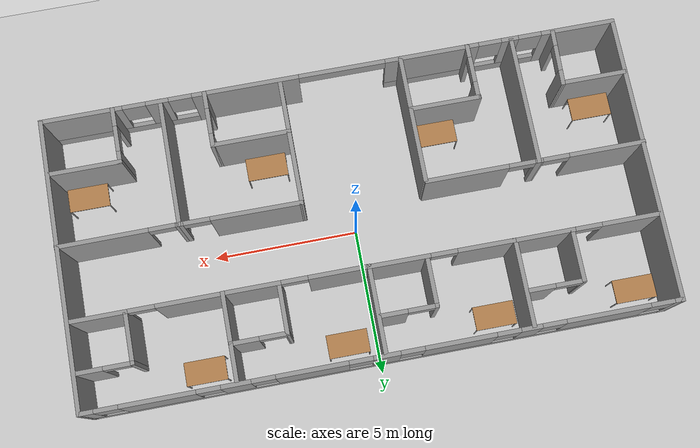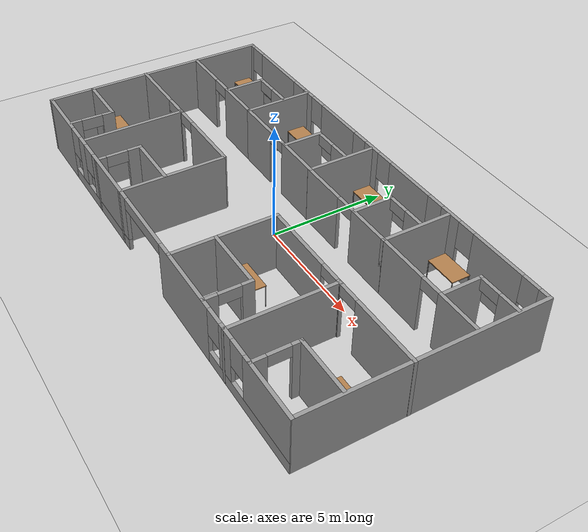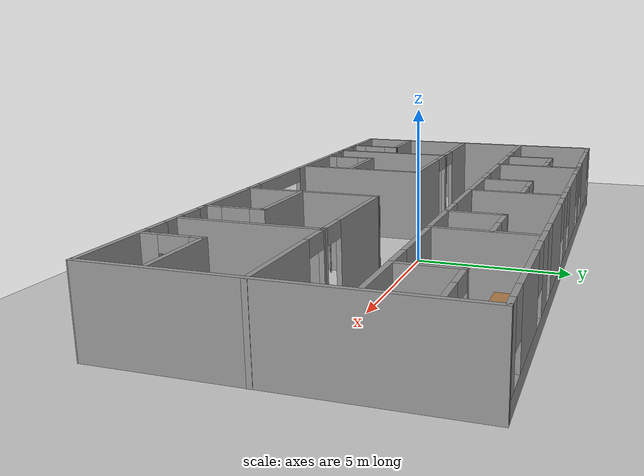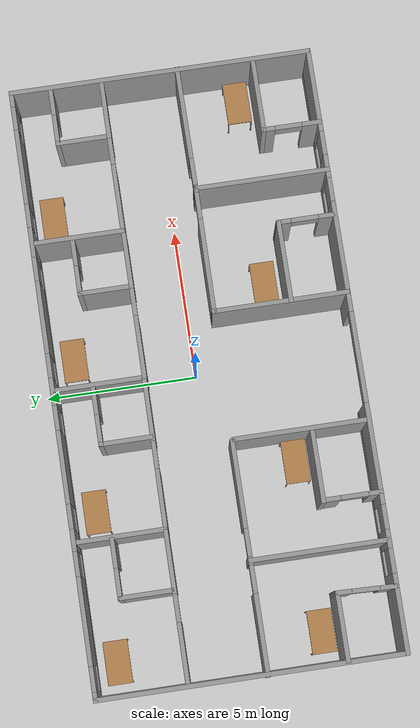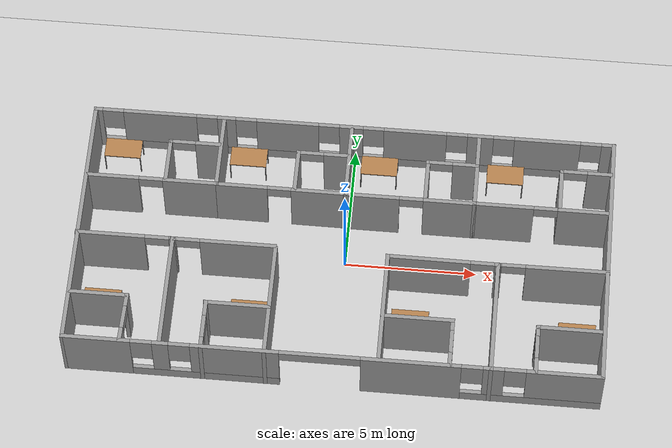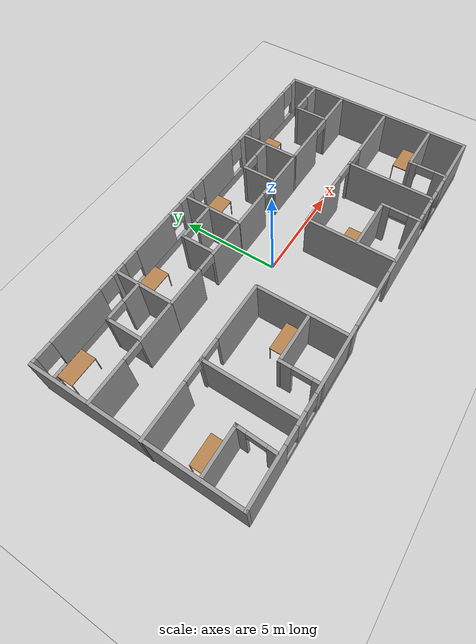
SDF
<sdf version="1.6">
 <world name="default">
  <light name="sun" type="directional">
   <pose>0 0 10 0 -0 0</pose>
   <diffuse>0.8 0.8 0.8 1</diffuse>
   <specular>0.1 0.1 0.1 1</specular>
   <attenuation>
    <range>1000</range>
    <constant>0.9</constant>
    <linear>0.01</linear>
    <quadratic>0.001</quadratic>
   </attenuation>
   <direction>-0.5 0.5 -1</direction>
  </light>
  <model name="ground_plane">
   <static>1</static>
   <link name="link">
    <collision name="collision">
     <geometry><plane><normal>0 0 1</normal><size>100 100</size></plane></geometry>
     <surface><friction><ode><mu>100</mu><mu2>50</mu2></ode></friction></surface>
    </collision>
    <visual name="visual">
     <cast_shadows>0</cast_shadows>
     <geometry><plane><normal>0 0 1</normal><size>100 100</size></plane></geometry>
     <material>
      <script><uri>file://media/materials/scripts/gazebo.material</uri><name>Gazebo/Grey</name></script>
     </material>
    </visual>
   </link>
  </model>
  <gravity>0 0 -9.8</gravity>
  <magnetic_field>6e-06 2.3e-05 -4.2e-05</magnetic_field>
  <atmosphere type="adiabatic"/>
  <physics name="default_physics" default="0" type="ode">
   <max_step_size>0.001</max_step_size>
   <real_time_factor>1</real_time_factor>
   <real_time_update_rate>1000</real_time_update_rate>
  </physics>
  <scene><ambient>0.4 0.4 0.4 1</ambient><background>0.7 0.7 0.7 1</background><shadows>1</shadows></scene>
  <spherical_coordinates>
   <surface_model>EARTH_WGS84</surface_model>
   <latitude_deg>0</latitude_deg>
   <longitude_deg>0</longitude_deg>
   <elevation>0</elevation>
   <heading_deg>0</heading_deg>
  </spherical_coordinates>
  <model name="resthome1_1">
   <pose>-0.062004 -0.275716 0 0 -0 0</pose>
   <link name="Wall_14">
    <pose>-7.47373 1.99162 0 0 -0 0</pose>
    <visual name="Wall_14_Visual_0">
     <pose>-1.4708 0 1.25 0 -0 0</pose>
     <geometry><box><size>2.0584 0.15 2.5</size></box></geometry>
     <material>
      <script><uri>file://media/materials/scripts/gazebo.material</uri><name>Gazebo/Grey</name></script>
      <ambient>1 1 1 1</ambient>
     </material>
    </visual>
    <collision name="Wall_14_Collision_0">
     <geometry><box><size>2.0584 0.15 2.5</size></box></geometry>
     <pose>-1.4708 0 1.25 0 -0 0</pose>
    </collision>
    <visual name="Wall_14_Visual_1">
     <pose>1.4792 0 1.25 0 -0 0</pose>
     <geometry><box><size>2.0416 0.15 2.5</size></box></geometry>
     <material>
      <script><uri>file://media/materials/scripts/gazebo.material</uri><name>Gazebo/Grey</name></script>
      <ambient>1 1 1 1</ambient>
     </material>
    </visual>
    <collision name="Wall_14_Collision_1">
     <geometry><box><size>2.0416 0.15 2.5</size></box></geometry>
     <pose>1.4792 0 1.25 0 -0 0</pose>
    </collision>
    <visual name="Wall_14_Visual_2">
     <pose>0.0084 0 2.25 0 -0 0</pose>
     <geometry><box><size>0.9 0.15 0.5</size></box></geometry>
     <material>
      <script><uri>file://media/materials/scripts/gazebo.material</uri><name>Gazebo/Grey</name></script>
      <ambient>1 1 1 1</ambient>
     </material>
    </visual>
    <collision name="Wall_14_Collision_2">
     <geometry><box><size>0.9 0.15 0.5</size></box></geometry>
     <pose>0.0084 0 2.25 0 -0 0</pose>
    </collision>
   </link>
   <link name="Wall_16">
    <collision name="Wall_16_Collision">
     <geometry><box><size>3 0.15 2.5</size></box></geometry>
     <pose>0 0 1.25 0 -0 0</pose>
    </collision>
    <visual name="Wall_16_Visual">
     <pose>0 0 1.25 0 -0 0</pose>
     <geometry><box><size>3 0.15 2.5</size></box></geometry>
     <material>
      <script><uri>file://media/materials/scripts/gazebo.material</uri><name>Gazebo/Grey</name></script>
      <ambient>1 1 1 1</ambient>
     </material>
    </visual>
    <pose>-4.9711 3.42586 0 0 0 -1.5708</pose>
   </link>
   <link name="Wall_24">
    <pose>-5.97761 3.7102 0 0 -0 0</pose>
    <visual name="Wall_24_Visual_0">
     <pose>-0.936133 0 1.25 0 -0 0</pose>
     <geometry><box><size>0.127734 0.15 2.5</size></box></geometry>
     <material>
      <script><uri>file://media/materials/scripts/gazebo.material</uri><name>Gazebo/Grey</name></script>
      <ambient>1 1 1 1</ambient>
     </material>
    </visual>
    <collision name="Wall_24_Collision_0">
     <geometry><box><size>0.127734 0.15 2.5</size></box></geometry>
     <pose>-0.936133 0 1.25 0 -0 0</pose>
    </collision>
    <visual name="Wall_24_Visual_1">
     <pose>0.513867 0 1.25 0 -0 0</pose>
     <geometry><box><size>0.972266 0.15 2.5</size></box></geometry>
     <material>
      <script><uri>file://media/materials/scripts/gazebo.material</uri><name>Gazebo/Grey</name></script>
      <ambient>1 1 1 1</ambient>
     </material>
    </visual>
    <collision name="Wall_24_Collision_1">
     <geometry><box><size>0.972266 0.15 2.5</size></box></geometry>
     <pose>0.513867 0 1.25 0 -0 0</pose>
    </collision>
    <visual name="Wall_24_Visual_2">
     <pose>-0.422266 0 2.25 0 -0 0</pose>
     <geometry><box><size>0.9 0.15 0.5</size></box></geometry>
     <material>
      <script><uri>file://media/materials/scripts/gazebo.material</uri><name>Gazebo/Grey</name></script>
      <ambient>1 1 1 1</ambient>
     </material>
    </visual>
    <collision name="Wall_24_Collision_2">
     <geometry><box><size>0.9 0.15 0.5</size></box></geometry>
     <pose>-0.422266 0 2.25 0 -0 0</pose>
    </collision>
   </link>
   <link name="Wall_26">
    <collision name="Wall_26_Collision">
     <geometry><box><size>1.75 0.15 2.5</size></box></geometry>
     <pose>0 0 1.25 0 -0 0</pose>
    </collision>
    <visual name="Wall_26_Visual">
     <pose>0 0 1.25 0 -0 0</pose>
     <geometry><box><size>1.75 0.15 2.5</size></box></geometry>
     <material>
      <script><uri>file://media/materials/scripts/gazebo.material</uri><name>Gazebo/Grey</name></script>
      <ambient>1 1 1 1</ambient>
     </material>
    </visual>
    <pose>-6.90261 2.8769 0 0 0 -1.5708</pose>
   </link>
   <link name="Wall_28">
    <pose>-2.49316 1.97557 0 0 0 -0.004147</pose>
    <visual name="Wall_28_Visual_0">
     <pose>-1.52052 0 1.25 0 -0 0</pose>
     <geometry><box><size>1.95897 0.15 2.5</size></box></geometry>
     <material>
      <script><uri>file://media/materials/scripts/gazebo.material</uri><name>Gazebo/Grey</name></script>
      <ambient>1 1 1 1</ambient>
     </material>
    </visual>
    <collision name="Wall_28_Collision_0">
     <geometry><box><size>1.95897 0.15 2.5</size></box></geometry>
     <pose>-1.52052 0 1.25 0 -0 0</pose>
    </collision>
    <visual name="Wall_28_Visual_1">
     <pose>1.42948 0 1.25 0 -0 0</pose>
     <geometry><box><size>2.14103 0.15 2.5</size></box></geometry>
     <material>
      <script><uri>file://media/materials/scripts/gazebo.material</uri><name>Gazebo/Grey</name></script>
      <ambient>1 1 1 1</ambient>
     </material>
    </visual>
    <collision name="Wall_28_Collision_1">
     <geometry><box><size>2.14103 0.15 2.5</size></box></geometry>
     <pose>1.42948 0 1.25 0 -0 0</pose>
    </collision>
    <visual name="Wall_28_Visual_2">
     <pose>-0.091033 0 2.25 0 -0 0</pose>
     <geometry><box><size>0.9 0.15 0.5</size></box></geometry>
     <material>
      <script><uri>file://media/materials/scripts/gazebo.material</uri><name>Gazebo/Grey</name></script>
      <ambient>1 1 1 1</ambient>
     </material>
    </visual>
    <collision name="Wall_28_Collision_2">
     <geometry><box><size>0.9 0.15 0.5</size></box></geometry>
     <pose>-0.091033 0 2.25 0 -0 0</pose>
    </collision>
   </link>
   <link name="Wall_3">
    <pose>0.005963 4.92634 0 0 -0 0.00165</pose>
    <visual name="Wall_3_Visual_0">
     <pose>-9.83255 0 1.25 0 -0 0</pose>
     <geometry><box><size>0.334932 0.15 2.5</size></box></geometry>
     <material>
      <script><uri>file://media/materials/scripts/gazebo.material</uri><name>Gazebo/Grey</name></script>
      <ambient>1 1 1 1</ambient>
     </material>
    </visual>
    <collision name="Wall_3_Collision_0">
     <geometry><box><size>0.334932 0.15 2.5</size></box></geometry>
     <pose>-9.83255 0 1.25 0 -0 0</pose>
    </collision>
    <visual name="Wall_3_Visual_1">
     <pose>0.167466 0 0.25 0 -0 0</pose>
     <geometry><box><size>19.6651 0.15 0.5</size></box></geometry>
     <material>
      <script><uri>file://media/materials/scripts/gazebo.material</uri><name>Gazebo/Grey</name></script>
      <ambient>1 1 1 1</ambient>
     </material>
    </visual>
    <collision name="Wall_3_Collision_1">
     <geometry><box><size>19.6651 0.15 0.5</size></box></geometry>
     <pose>0.167466 0 0.25 0 -0 0</pose>
    </collision>
    <visual name="Wall_3_Visual_2">
     <pose>-7.45661 0 1.5 0 -0 0</pose>
     <geometry><box><size>2.81693 0.15 2</size></box></geometry>
     <material>
      <script><uri>file://media/materials/scripts/gazebo.material</uri><name>Gazebo/Grey</name></script>
      <ambient>1 1 1 1</ambient>
     </material>
    </visual>
    <collision name="Wall_3_Collision_2">
     <geometry><box><size>2.81693 0.15 2</size></box></geometry>
     <pose>-7.45661 0 1.5 0 -0 0</pose>
    </collision>
    <visual name="Wall_3_Visual_3">
     <pose>-4.89389 0 1.5 0 -0 0</pose>
     <geometry><box><size>0.708514 0.15 2</size></box></geometry>
     <material>
      <script><uri>file://media/materials/scripts/gazebo.material</uri><name>Gazebo/Grey</name></script>
      <ambient>1 1 1 1</ambient>
     </material>
    </visual>
    <collision name="Wall_3_Collision_3">
     <geometry><box><size>0.708514 0.15 2</size></box></geometry>
     <pose>-4.89389 0 1.5 0 -0 0</pose>
    </collision>
    <visual name="Wall_3_Visual_4">
     <pose>-2.54776 0 1.5 0 -0 0</pose>
     <geometry><box><size>2.38375 0.15 2</size></box></geometry>
     <material>
      <script><uri>file://media/materials/scripts/gazebo.material</uri><name>Gazebo/Grey</name></script>
      <ambient>1 1 1 1</ambient>
     </material>
    </visual>
    <collision name="Wall_3_Collision_4">
     <geometry><box><size>2.38375 0.15 2</size></box></geometry>
     <pose>-2.54776 0 1.5 0 -0 0</pose>
    </collision>
    <visual name="Wall_3_Visual_5">
     <pose>-0.10317 0 1.5 0 -0 0</pose>
     <geometry><box><size>0.905421 0.15 2</size></box></geometry>
     <material>
      <script><uri>file://media/materials/scripts/gazebo.material</uri><name>Gazebo/Grey</name></script>
      <ambient>1 1 1 1</ambient>
     </material>
    </visual>
    <collision name="Wall_3_Collision_5">
     <geometry><box><size>0.905421 0.15 2</size></box></geometry>
     <pose>-0.10317 0 1.5 0 -0 0</pose>
    </collision>
    <visual name="Wall_3_Visual_6">
     <pose>2.35056 0 1.5 0 -0 0</pose>
     <geometry><box><size>2.40204 0.15 2</size></box></geometry>
     <material>
      <script><uri>file://media/materials/scripts/gazebo.material</uri><name>Gazebo/Grey</name></script>
      <ambient>1 1 1 1</ambient>
     </material>
    </visual>
    <collision name="Wall_3_Collision_6">
     <geometry><box><size>2.40204 0.15 2</size></box></geometry>
     <pose>2.35056 0 1.5 0 -0 0</pose>
    </collision>
    <visual name="Wall_3_Visual_7">
     <pose>4.84703 0 1.5 0 -0 0</pose>
     <geometry><box><size>0.990901 0.15 2</size></box></geometry>
     <material>
      <script><uri>file://media/materials/scripts/gazebo.material</uri><name>Gazebo/Grey</name></script>
      <ambient>1 1 1 1</ambient>
     </material>
    </visual>
    <collision name="Wall_3_Collision_7">
     <geometry><box><size>0.990901 0.15 2</size></box></geometry>
     <pose>4.84703 0 1.5 0 -0 0</pose>
    </collision>
    <visual name="Wall_3_Visual_8">
     <pose>7.40109 0 1.5 0 -0 0</pose>
     <geometry><box><size>2.51722 0.15 2</size></box></geometry>
     <material>
      <script><uri>file://media/materials/scripts/gazebo.material</uri><name>Gazebo/Grey</name></script>
      <ambient>1 1 1 1</ambient>
     </material>
    </visual>
    <collision name="Wall_3_Collision_8">
     <geometry><box><size>2.51722 0.15 2</size></box></geometry>
     <pose>7.40109 0 1.5 0 -0 0</pose>
    </collision>
    <visual name="Wall_3_Visual_9">
     <pose>9.72986 0 1.5 0 -0 0</pose>
     <geometry><box><size>0.540311 0.15 2</size></box></geometry>
     <material>
      <script><uri>file://media/materials/scripts/gazebo.material</uri><name>Gazebo/Grey</name></script>
      <ambient>1 1 1 1</ambient>
     </material>
    </visual>
    <collision name="Wall_3_Collision_9">
     <geometry><box><size>0.540311 0.15 2</size></box></geometry>
     <pose>9.72986 0 1.5 0 -0 0</pose>
    </collision>
    <visual name="Wall_3_Visual_10">
     <pose>-9.26508 0 1.9 0 -0 0</pose>
     <geometry><box><size>0.8 0.15 1.2</size></box></geometry>
     <material>
      <script><uri>file://media/materials/scripts/gazebo.material</uri><name>Gazebo/Grey</name></script>
      <ambient>1 1 1 1</ambient>
     </material>
    </visual>
    <collision name="Wall_3_Collision_10">
     <geometry><box><size>0.8 0.15 1.2</size></box></geometry>
     <pose>-9.26508 0 1.9 0 -0 0</pose>
    </collision>
    <visual name="Wall_3_Visual_11">
     <pose>-5.64815 0 1.9 0 -0 0</pose>
     <geometry><box><size>0.8 0.15 1.2</size></box></geometry>
     <material>
      <script><uri>file://media/materials/scripts/gazebo.material</uri><name>Gazebo/Grey</name></script>
      <ambient>1 1 1 1</ambient>
     </material>
    </visual>
    <collision name="Wall_3_Collision_11">
     <geometry><box><size>0.8 0.15 1.2</size></box></geometry>
     <pose>-5.64815 0 1.9 0 -0 0</pose>
    </collision>
    <visual name="Wall_3_Visual_12">
     <pose>-4.13963 0 1.9 0 -0 0</pose>
     <geometry><box><size>0.8 0.15 1.2</size></box></geometry>
     <material>
      <script><uri>file://media/materials/scripts/gazebo.material</uri><name>Gazebo/Grey</name></script>
      <ambient>1 1 1 1</ambient>
     </material>
    </visual>
    <collision name="Wall_3_Collision_12">
     <geometry><box><size>0.8 0.15 1.2</size></box></geometry>
     <pose>-4.13963 0 1.9 0 -0 0</pose>
    </collision>
    <visual name="Wall_3_Visual_13">
     <pose>-0.95588 0 1.9 0 -0 0</pose>
     <geometry><box><size>0.8 0.15 1.2</size></box></geometry>
     <material>
      <script><uri>file://media/materials/scripts/gazebo.material</uri><name>Gazebo/Grey</name></script>
      <ambient>1 1 1 1</ambient>
     </material>
    </visual>
    <collision name="Wall_3_Collision_13">
     <geometry><box><size>0.8 0.15 1.2</size></box></geometry>
     <pose>-0.95588 0 1.9 0 -0 0</pose>
    </collision>
    <visual name="Wall_3_Visual_14">
     <pose>0.749541 0 1.9 0 -0 0</pose>
     <geometry><box><size>0.8 0.15 1.2</size></box></geometry>
     <material>
      <script><uri>file://media/materials/scripts/gazebo.material</uri><name>Gazebo/Grey</name></script>
      <ambient>1 1 1 1</ambient>
     </material>
    </visual>
    <collision name="Wall_3_Collision_14">
     <geometry><box><size>0.8 0.15 1.2</size></box></geometry>
     <pose>0.749541 0 1.9 0 -0 0</pose>
    </collision>
    <visual name="Wall_3_Visual_15">
     <pose>3.95158 0 1.9 0 -0 0</pose>
     <geometry><box><size>0.8 0.15 1.2</size></box></geometry>
     <material>
      <script><uri>file://media/materials/scripts/gazebo.material</uri><name>Gazebo/Grey</name></script>
      <ambient>1 1 1 1</ambient>
     </material>
    </visual>
    <collision name="Wall_3_Collision_15">
     <geometry><box><size>0.8 0.15 1.2</size></box></geometry>
     <pose>3.95158 0 1.9 0 -0 0</pose>
    </collision>
    <visual name="Wall_3_Visual_16">
     <pose>5.74248 0 1.9 0 -0 0</pose>
     <geometry><box><size>0.8 0.15 1.2</size></box></geometry>
     <material>
      <script><uri>file://media/materials/scripts/gazebo.material</uri><name>Gazebo/Grey</name></script>
      <ambient>1 1 1 1</ambient>
     </material>
    </visual>
    <collision name="Wall_3_Collision_16">
     <geometry><box><size>0.8 0.15 1.2</size></box></geometry>
     <pose>5.74248 0 1.9 0 -0 0</pose>
    </collision>
    <visual name="Wall_3_Visual_17">
     <pose>9.0597 0 1.9 0 -0 0</pose>
     <geometry><box><size>0.8 0.15 1.2</size></box></geometry>
     <material>
      <script><uri>file://media/materials/scripts/gazebo.material</uri><name>Gazebo/Grey</name></script>
      <ambient>1 1 1 1</ambient>
     </material>
    </visual>
    <collision name="Wall_3_Collision_17">
     <geometry><box><size>0.8 0.15 1.2</size></box></geometry>
     <pose>9.0597 0 1.9 0 -0 0</pose>
    </collision>
   </link>
   <link name="Wall_30">
    <collision name="Wall_30_Collision">
     <geometry><box><size>3 0.15 2.5</size></box></geometry>
     <pose>0 0 1.25 0 -0 0</pose>
    </collision>
    <visual name="Wall_30_Visual">
     <pose>0 0 1.25 0 -0 0</pose>
     <geometry><box><size>3 0.15 2.5</size></box></geometry>
     <material>
      <script><uri>file://media/materials/scripts/gazebo.material</uri><name>Gazebo/Grey</name></script>
      <ambient>1 1 1 1</ambient>
     </material>
    </visual>
    <pose>-0.068165 3.39051 0 0 -0 1.5708</pose>
   </link>
   <link name="Wall_32">
    <pose>-1.07625 3.63494 0 0 -0 3.14159</pose>
    <visual name="Wall_32_Visual_0">
     <pose>-0.519401 0 1.25 0 -0 0</pose>
     <geometry><box><size>0.961198 0.15 2.5</size></box></geometry>
     <material>
      <script><uri>file://media/materials/scripts/gazebo.material</uri><name>Gazebo/Grey</name></script>
      <ambient>1 1 1 1</ambient>
     </material>
    </visual>
    <collision name="Wall_32_Collision_0">
     <geometry><box><size>0.961198 0.15 2.5</size></box></geometry>
     <pose>-0.519401 0 1.25 0 -0 0</pose>
    </collision>
    <visual name="Wall_32_Visual_1">
     <pose>0.930599 0 1.25 0 -0 0</pose>
     <geometry><box><size>0.138802 0.15 2.5</size></box></geometry>
     <material>
      <script><uri>file://media/materials/scripts/gazebo.material</uri><name>Gazebo/Grey</name></script>
      <ambient>1 1 1 1</ambient>
     </material>
    </visual>
    <collision name="Wall_32_Collision_1">
     <geometry><box><size>0.138802 0.15 2.5</size></box></geometry>
     <pose>0.930599 0 1.25 0 -0 0</pose>
    </collision>
    <visual name="Wall_32_Visual_2">
     <pose>0.411198 0 2.25 0 -0 0</pose>
     <geometry><box><size>0.9 0.15 0.5</size></box></geometry>
     <material>
      <script><uri>file://media/materials/scripts/gazebo.material</uri><name>Gazebo/Grey</name></script>
      <ambient>1 1 1 1</ambient>
     </material>
    </visual>
    <collision name="Wall_32_Collision_2">
     <geometry><box><size>0.9 0.15 0.5</size></box></geometry>
     <pose>0.411198 0 2.25 0 -0 0</pose>
    </collision>
   </link>
   <link name="Wall_34">
    <collision name="Wall_34_Collision">
     <geometry><box><size>1.75 0.15 2.5</size></box></geometry>
     <pose>0 0 1.25 0 -0 0</pose>
    </collision>
    <visual name="Wall_34_Visual">
     <pose>0 0 1.25 0 -0 0</pose>
     <geometry><box><size>1.75 0.15 2.5</size></box></geometry>
     <material>
      <script><uri>file://media/materials/scripts/gazebo.material</uri><name>Gazebo/Grey</name></script>
      <ambient>1 1 1 1</ambient>
     </material>
    </visual>
    <pose>-2.00125 2.83494 0 0 0 -1.5708</pose>
   </link>
   <link name="Wall_36">
    <pose>2.38239 1.95177 0 0 -0 0</pose>
    <visual name="Wall_36_Visual_0">
     <pose>-1.45559 0 1.25 0 -0 0</pose>
     <geometry><box><size>2.08882 0.15 2.5</size></box></geometry>
     <material>
      <script><uri>file://media/materials/scripts/gazebo.material</uri><name>Gazebo/Grey</name></script>
      <ambient>1 1 1 1</ambient>
     </material>
    </visual>
    <collision name="Wall_36_Collision_0">
     <geometry><box><size>2.08882 0.15 2.5</size></box></geometry>
     <pose>-1.45559 0 1.25 0 -0 0</pose>
    </collision>
    <visual name="Wall_36_Visual_1">
     <pose>1.49441 0 1.25 0 -0 0</pose>
     <geometry><box><size>2.01118 0.15 2.5</size></box></geometry>
     <material>
      <script><uri>file://media/materials/scripts/gazebo.material</uri><name>Gazebo/Grey</name></script>
      <ambient>1 1 1 1</ambient>
     </material>
    </visual>
    <collision name="Wall_36_Collision_1">
     <geometry><box><size>2.01118 0.15 2.5</size></box></geometry>
     <pose>1.49441 0 1.25 0 -0 0</pose>
    </collision>
    <visual name="Wall_36_Visual_2">
     <pose>0.038817 0 2.25 0 -0 0</pose>
     <geometry><box><size>0.9 0.15 0.5</size></box></geometry>
     <material>
      <script><uri>file://media/materials/scripts/gazebo.material</uri><name>Gazebo/Grey</name></script>
      <ambient>1 1 1 1</ambient>
     </material>
    </visual>
    <collision name="Wall_36_Collision_2">
     <geometry><box><size>0.9 0.15 0.5</size></box></geometry>
     <pose>0.038817 0 2.25 0 -0 0</pose>
    </collision>
   </link>
   <link name="Wall_38">
    <collision name="Wall_38_Collision">
     <geometry><box><size>3 0.15 2.5</size></box></geometry>
     <pose>0 0 1.25 0 -0 0</pose>
    </collision>
    <visual name="Wall_38_Visual">
     <pose>0 0 1.25 0 -0 0</pose>
     <geometry><box><size>3 0.15 2.5</size></box></geometry>
     <material>
      <script><uri>file://media/materials/scripts/gazebo.material</uri><name>Gazebo/Grey</name></script>
      <ambient>1 1 1 1</ambient>
     </material>
    </visual>
    <pose>4.80738 3.37677 0 0 -0 1.5708</pose>
   </link>
   <link name="Wall_40">
    <pose>3.86877 3.62473 0 0 -0 3.14159</pose>
    <visual name="Wall_40_Visual_0">
     <pose>-0.503106 0 1.25 0 -0 0</pose>
     <geometry><box><size>0.993788 0.15 2.5</size></box></geometry>
     <material>
      <script><uri>file://media/materials/scripts/gazebo.material</uri><name>Gazebo/Grey</name></script>
      <ambient>1 1 1 1</ambient>
     </material>
    </visual>
    <collision name="Wall_40_Collision_0">
     <geometry><box><size>0.993788 0.15 2.5</size></box></geometry>
     <pose>-0.503106 0 1.25 0 -0 0</pose>
    </collision>
    <visual name="Wall_40_Visual_1">
     <pose>0.946894 0 1.25 0 -0 0</pose>
     <geometry><box><size>0.106212 0.15 2.5</size></box></geometry>
     <material>
      <script><uri>file://media/materials/scripts/gazebo.material</uri><name>Gazebo/Grey</name></script>
      <ambient>1 1 1 1</ambient>
     </material>
    </visual>
    <collision name="Wall_40_Collision_1">
     <geometry><box><size>0.106212 0.15 2.5</size></box></geometry>
     <pose>0.946894 0 1.25 0 -0 0</pose>
    </collision>
    <visual name="Wall_40_Visual_2">
     <pose>0.443788 0 2.25 0 -0 0</pose>
     <geometry><box><size>0.9 0.15 0.5</size></box></geometry>
     <material>
      <script><uri>file://media/materials/scripts/gazebo.material</uri><name>Gazebo/Grey</name></script>
      <ambient>1 1 1 1</ambient>
     </material>
    </visual>
    <collision name="Wall_40_Collision_2">
     <geometry><box><size>0.9 0.15 0.5</size></box></geometry>
     <pose>0.443788 0 2.25 0 -0 0</pose>
    </collision>
   </link>
   <link name="Wall_41">
    <collision name="Wall_41_Collision">
     <geometry><box><size>1.75 0.15 2.5</size></box></geometry>
     <pose>0 0 1.25 0 -0 0</pose>
    </collision>
    <visual name="Wall_41_Visual">
     <pose>0 0 1.25 0 -0 0</pose>
     <geometry><box><size>1.75 0.15 2.5</size></box></geometry>
     <material>
      <script><uri>file://media/materials/scripts/gazebo.material</uri><name>Gazebo/Grey</name></script>
      <ambient>1 1 1 1</ambient>
     </material>
    </visual>
    <pose>2.94377 2.82473 0 0 0 -1.5708</pose>
   </link>
   <link name="Wall_43">
    <pose>7.37031 1.96098 0 0 -0 0</pose>
    <visual name="Wall_43_Visual_0">
     <pose>-1.4125 0 1.25 0 -0 0</pose>
     <geometry><box><size>2.175 0.15 2.5</size></box></geometry>
     <material>
      <script><uri>file://media/materials/scripts/gazebo.material</uri><name>Gazebo/Grey</name></script>
      <ambient>1 1 1 1</ambient>
     </material>
    </visual>
    <collision name="Wall_43_Collision_0">
     <geometry><box><size>2.175 0.15 2.5</size></box></geometry>
     <pose>-1.4125 0 1.25 0 -0 0</pose>
    </collision>
    <visual name="Wall_43_Visual_1">
     <pose>1.5375 0 1.25 0 -0 0</pose>
     <geometry><box><size>1.925 0.15 2.5</size></box></geometry>
     <material>
      <script><uri>file://media/materials/scripts/gazebo.material</uri><name>Gazebo/Grey</name></script>
      <ambient>1 1 1 1</ambient>
     </material>
    </visual>
    <collision name="Wall_43_Collision_1">
     <geometry><box><size>1.925 0.15 2.5</size></box></geometry>
     <pose>1.5375 0 1.25 0 -0 0</pose>
    </collision>
    <visual name="Wall_43_Visual_2">
     <pose>0.125 0 2.25 0 -0 0</pose>
     <geometry><box><size>0.9 0.15 0.5</size></box></geometry>
     <material>
      <script><uri>file://media/materials/scripts/gazebo.material</uri><name>Gazebo/Grey</name></script>
      <ambient>1 1 1 1</ambient>
     </material>
    </visual>
    <collision name="Wall_43_Collision_2">
     <geometry><box><size>0.9 0.15 0.5</size></box></geometry>
     <pose>0.125 0 2.25 0 -0 0</pose>
    </collision>
   </link>
   <link name="Wall_45">
    <pose>8.94031 3.65098 0 0 -0 3.14159</pose>
    <visual name="Wall_45_Visual_0">
     <pose>-0.5225 0 1.25 0 -0 0</pose>
     <geometry><box><size>0.955 0.15 2.5</size></box></geometry>
     <material>
      <script><uri>file://media/materials/scripts/gazebo.material</uri><name>Gazebo/Grey</name></script>
      <ambient>1 1 1 1</ambient>
     </material>
    </visual>
    <collision name="Wall_45_Collision_0">
     <geometry><box><size>0.955 0.15 2.5</size></box></geometry>
     <pose>-0.5225 0 1.25 0 -0 0</pose>
    </collision>
    <visual name="Wall_45_Visual_1">
     <pose>0.9275 0 1.25 0 -0 0</pose>
     <geometry><box><size>0.145 0.15 2.5</size></box></geometry>
     <material>
      <script><uri>file://media/materials/scripts/gazebo.material</uri><name>Gazebo/Grey</name></script>
      <ambient>1 1 1 1</ambient>
     </material>
    </visual>
    <collision name="Wall_45_Collision_1">
     <geometry><box><size>0.145 0.15 2.5</size></box></geometry>
     <pose>0.9275 0 1.25 0 -0 0</pose>
    </collision>
    <visual name="Wall_45_Visual_2">
     <pose>0.405 0 2.25 0 -0 0</pose>
     <geometry><box><size>0.9 0.15 0.5</size></box></geometry>
     <material>
      <script><uri>file://media/materials/scripts/gazebo.material</uri><name>Gazebo/Grey</name></script>
      <ambient>1 1 1 1</ambient>
     </material>
    </visual>
    <collision name="Wall_45_Collision_2">
     <geometry><box><size>0.9 0.15 0.5</size></box></geometry>
     <pose>0.405 0 2.25 0 -0 0</pose>
    </collision>
   </link>
   <link name="Wall_46">
    <collision name="Wall_46_Collision">
     <geometry><box><size>1.75 0.15 2.5</size></box></geometry>
     <pose>0 0 1.25 0 -0 0</pose>
    </collision>
    <visual name="Wall_46_Visual">
     <pose>0 0 1.25 0 -0 0</pose>
     <geometry><box><size>1.75 0.15 2.5</size></box></geometry>
     <material>
      <script><uri>file://media/materials/scripts/gazebo.material</uri><name>Gazebo/Grey</name></script>
      <ambient>1 1 1 1</ambient>
     </material>
    </visual>
    <pose>8.01531 2.85098 0 0 0 -1.5708</pose>
   </link>
   <link name="Wall_50">
    <collision name="Wall_50_Collision">
     <geometry><box><size>10 0.15 2.5</size></box></geometry>
     <pose>0 0 1.25 0 -0 0</pose>
    </collision>
    <visual name="Wall_50_Visual">
     <pose>0 0 1.25 0 -0 0</pose>
     <geometry><box><size>10 0.15 2.5</size></box></geometry>
     <material>
      <script><uri>file://media/materials/scripts/gazebo.material</uri><name>Gazebo/Grey</name></script>
      <ambient>1 1 1 1</ambient>
     </material>
    </visual>
    <pose>-9.91922 -0.015034 0 0 0 -1.5708</pose>
   </link>
   <link name="Wall_52">
    <collision name="Wall_52_Collision">
     <geometry><box><size>10 0.15 2.5</size></box></geometry>
     <pose>0 0 1.25 0 -0 0</pose>
    </collision>
    <visual name="Wall_52_Visual">
     <pose>0 0 1.25 0 -0 0</pose>
     <geometry><box><size>10 0.15 2.5</size></box></geometry>
     <material>
      <script><uri>file://media/materials/scripts/gazebo.material</uri><name>Gazebo/Grey</name></script>
      <ambient>1 1 1 1</ambient>
     </material>
    </visual>
    <pose>9.93114 0.017719 0 0 0 -1.5708</pose>
   </link>
   <link name="Wall_56">
    <pose>0.005783 -4.94003 0 0 -0 0</pose>
    <visual name="Wall_56_Visual_0">
     <pose>-8.70721 0 1.25 0 -0 0</pose>
     <geometry><box><size>2.58559 0.15 2.5</size></box></geometry>
     <material>
      <script><uri>file://media/materials/scripts/gazebo.material</uri><name>Gazebo/Grey</name></script>
      <ambient>1 1 1 1</ambient>
     </material>
    </visual>
    <collision name="Wall_56_Collision_0">
     <geometry><box><size>2.58559 0.15 2.5</size></box></geometry>
     <pose>-8.70721 0 1.25 0 -0 0</pose>
    </collision>
    <visual name="Wall_56_Visual_1">
     <pose>2.91559 0 1.25 0 -0 0</pose>
     <geometry><box><size>3.7 0.15 2.5</size></box></geometry>
     <material>
      <script><uri>file://media/materials/scripts/gazebo.material</uri><name>Gazebo/Grey</name></script>
      <ambient>1 1 1 1</ambient>
     </material>
    </visual>
    <collision name="Wall_56_Collision_1">
     <geometry><box><size>3.7 0.15 2.5</size></box></geometry>
     <pose>2.91559 0 1.25 0 -0 0</pose>
    </collision>
    <visual name="Wall_56_Visual_2">
     <pose>-4.67441 0 0.25 0 -0 0</pose>
     <geometry><box><size>5.48 0.15 0.5</size></box></geometry>
     <material>
      <script><uri>file://media/materials/scripts/gazebo.material</uri><name>Gazebo/Grey</name></script>
      <ambient>1 1 1 1</ambient>
     </material>
    </visual>
    <collision name="Wall_56_Collision_2">
     <geometry><box><size>5.48 0.15 0.5</size></box></geometry>
     <pose>-4.67441 0 0.25 0 -0 0</pose>
    </collision>
    <visual name="Wall_56_Visual_3">
     <pose>7.3828 0 0.25 0 -0 0</pose>
     <geometry><box><size>5.23441 0.15 0.5</size></box></geometry>
     <material>
      <script><uri>file://media/materials/scripts/gazebo.material</uri><name>Gazebo/Grey</name></script>
      <ambient>1 1 1 1</ambient>
     </material>
    </visual>
    <collision name="Wall_56_Collision_3">
     <geometry><box><size>5.23441 0.15 0.5</size></box></geometry>
     <pose>7.3828 0 0.25 0 -0 0</pose>
    </collision>
    <visual name="Wall_56_Visual_4">
     <pose>-6.31441 0 1.5 0 -0 0</pose>
     <geometry><box><size>0.6 0.15 2</size></box></geometry>
     <material>
      <script><uri>file://media/materials/scripts/gazebo.material</uri><name>Gazebo/Grey</name></script>
      <ambient>1 1 1 1</ambient>
     </material>
    </visual>
    <collision name="Wall_56_Collision_4">
     <geometry><box><size>0.6 0.15 2</size></box></geometry>
     <pose>-6.31441 0 1.5 0 -0 0</pose>
    </collision>
    <visual name="Wall_56_Visual_5">
     <pose>-3.57441 0 1.5 0 -0 0</pose>
     <geometry><box><size>3.28 0.15 2</size></box></geometry>
     <material>
      <script><uri>file://media/materials/scripts/gazebo.material</uri><name>Gazebo/Grey</name></script>
      <ambient>1 1 1 1</ambient>
     </material>
    </visual>
    <collision name="Wall_56_Collision_5">
     <geometry><box><size>3.28 0.15 2</size></box></geometry>
     <pose>-3.57441 0 1.5 0 -0 0</pose>
    </collision>
    <visual name="Wall_56_Visual_6">
     <pose>-3.57441 0 1.5 0 -0 0</pose>
     <geometry><box><size>3.28 0.15 2</size></box></geometry>
     <material>
      <script><uri>file://media/materials/scripts/gazebo.material</uri><name>Gazebo/Grey</name></script>
      <ambient>1 1 1 1</ambient>
     </material>
    </visual>
    <collision name="Wall_56_Collision_6">
     <geometry><box><size>3.28 0.15 2</size></box></geometry>
     <pose>-3.57441 0 1.5 0 -0 0</pose>
    </collision>
    <visual name="Wall_56_Visual_7">
     <pose>5.95559 0 1.5 0 -0 0</pose>
     <geometry><box><size>0.78 0.15 2</size></box></geometry>
     <material>
      <script><uri>file://media/materials/scripts/gazebo.material</uri><name>Gazebo/Grey</name></script>
      <ambient>1 1 1 1</ambient>
     </material>
    </visual>
    <collision name="Wall_56_Collision_7">
     <geometry><box><size>0.78 0.15 2</size></box></geometry>
     <pose>5.95559 0 1.5 0 -0 0</pose>
    </collision>
    <visual name="Wall_56_Visual_8">
     <pose>8.5728 0 1.5 0 -0 0</pose>
     <geometry><box><size>2.85441 0.15 2</size></box></geometry>
     <material>
      <script><uri>file://media/materials/scripts/gazebo.material</uri><name>Gazebo/Grey</name></script>
      <ambient>1 1 1 1</ambient>
     </material>
    </visual>
    <collision name="Wall_56_Collision_8">
     <geometry><box><size>2.85441 0.15 2</size></box></geometry>
     <pose>8.5728 0 1.5 0 -0 0</pose>
    </collision>
    <visual name="Wall_56_Visual_9">
     <pose>-7.01441 0 1.9 0 -0 0</pose>
     <geometry><box><size>0.8 0.15 1.2</size></box></geometry>
     <material>
      <script><uri>file://media/materials/scripts/gazebo.material</uri><name>Gazebo/Grey</name></script>
      <ambient>1 1 1 1</ambient>
     </material>
    </visual>
    <collision name="Wall_56_Collision_9">
     <geometry><box><size>0.8 0.15 1.2</size></box></geometry>
     <pose>-7.01441 0 1.9 0 -0 0</pose>
    </collision>
    <visual name="Wall_56_Visual_10">
     <pose>5.16559 0 1.9 0 -0 0</pose>
     <geometry><box><size>0.8 0.15 1.2</size></box></geometry>
     <material>
      <script><uri>file://media/materials/scripts/gazebo.material</uri><name>Gazebo/Grey</name></script>
      <ambient>1 1 1 1</ambient>
     </material>
    </visual>
    <collision name="Wall_56_Collision_10">
     <geometry><box><size>0.8 0.15 1.2</size></box></geometry>
     <pose>5.16559 0 1.9 0 -0 0</pose>
    </collision>
    <visual name="Wall_56_Visual_11">
     <pose>-5.61441 0 1.9 0 -0 0</pose>
     <geometry><box><size>0.8 0.15 1.2</size></box></geometry>
     <material>
      <script><uri>file://media/materials/scripts/gazebo.material</uri><name>Gazebo/Grey</name></script>
      <ambient>1 1 1 1</ambient>
     </material>
    </visual>
    <collision name="Wall_56_Collision_11">
     <geometry><box><size>0.8 0.15 1.2</size></box></geometry>
     <pose>-5.61441 0 1.9 0 -0 0</pose>
    </collision>
    <visual name="Wall_56_Visual_12">
     <pose>6.74559 0 1.9 0 -0 0</pose>
     <geometry><box><size>0.8 0.15 1.2</size></box></geometry>
     <material>
      <script><uri>file://media/materials/scripts/gazebo.material</uri><name>Gazebo/Grey</name></script>
      <ambient>1 1 1 1</ambient>
     </material>
    </visual>
    <collision name="Wall_56_Collision_12">
     <geometry><box><size>0.8 0.15 1.2</size></box></geometry>
     <pose>6.74559 0 1.9 0 -0 0</pose>
    </collision>
    <visual name="Wall_56_Visual_13">
     <pose>-0.434409 0 2.25 0 -0 0</pose>
     <geometry><box><size>3 0.15 0.5</size></box></geometry>
     <material>
      <script><uri>file://media/materials/scripts/gazebo.material</uri><name>Gazebo/Grey</name></script>
      <ambient>1 1 1 1</ambient>
     </material>
    </visual>
    <collision name="Wall_56_Collision_13">
     <geometry><box><size>3 0.15 0.5</size></box></geometry>
     <pose>-0.434409 0 2.25 0 -0 0</pose>
    </collision>
    <visual name="Wall_56_Visual_14">
     <pose>-0.434409 0 2.25 0 -0 0</pose>
     <geometry><box><size>3 0.15 0.5</size></box></geometry>
     <material>
      <script><uri>file://media/materials/scripts/gazebo.material</uri><name>Gazebo/Grey</name></script>
      <ambient>1 1 1 1</ambient>
     </material>
    </visual>
    <collision name="Wall_56_Collision_14">
     <geometry><box><size>3 0.15 0.5</size></box></geometry>
     <pose>-0.434409 0 2.25 0 -0 0</pose>
    </collision>
   </link>
   <link name="Wall_58">
    <pose>-8.14174 -0.522095 0 0 -0 0</pose>
    <visual name="Wall_58_Visual_0">
     <pose>-0.559641 0 1.25 0 -0 0</pose>
     <geometry><box><size>2.63072 0.15 2.5</size></box></geometry>
     <material>
      <script><uri>file://media/materials/scripts/gazebo.material</uri><name>Gazebo/Grey</name></script>
      <ambient>1 1 1 1</ambient>
     </material>
    </visual>
    <collision name="Wall_58_Collision_0">
     <geometry><box><size>2.63072 0.15 2.5</size></box></geometry>
     <pose>-0.559641 0 1.25 0 -0 0</pose>
    </collision>
    <visual name="Wall_58_Visual_1">
     <pose>1.76536 0 1.25 0 -0 0</pose>
     <geometry><box><size>0.219282 0.15 2.5</size></box></geometry>
     <material>
      <script><uri>file://media/materials/scripts/gazebo.material</uri><name>Gazebo/Grey</name></script>
      <ambient>1 1 1 1</ambient>
     </material>
    </visual>
    <collision name="Wall_58_Collision_1">
     <geometry><box><size>0.219282 0.15 2.5</size></box></geometry>
     <pose>1.76536 0 1.25 0 -0 0</pose>
    </collision>
    <visual name="Wall_58_Visual_2">
     <pose>1.20572 0 2.25 0 -0 0</pose>
     <geometry><box><size>0.9 0.15 0.5</size></box></geometry>
     <material>
      <script><uri>file://media/materials/scripts/gazebo.material</uri><name>Gazebo/Grey</name></script>
      <ambient>1 1 1 1</ambient>
     </material>
    </visual>
    <collision name="Wall_58_Collision_2">
     <geometry><box><size>0.9 0.15 0.5</size></box></geometry>
     <pose>1.20572 0 2.25 0 -0 0</pose>
    </collision>
   </link>
   <link name="Wall_59">
    <collision name="Wall_59_Collision">
     <geometry><box><size>4.5 0.15 2.5</size></box></geometry>
     <pose>0 0 1.25 0 -0 0</pose>
    </collision>
    <visual name="Wall_59_Visual">
     <pose>0 0 1.25 0 -0 0</pose>
     <geometry><box><size>4.5 0.15 2.5</size></box></geometry>
     <material>
      <script><uri>file://media/materials/scripts/gazebo.material</uri><name>Gazebo/Grey</name></script>
      <ambient>1 1 1 1</ambient>
     </material>
    </visual>
    <pose>-6.34174 -2.6971 0 0 0 -1.5708</pose>
   </link>
   <link name="Wall_72">
    <pose>-4.43674 -0.522095 0 0 -0 3.14159</pose>
    <visual name="Wall_72_Visual_0">
     <pose>-0.559058 0 1.25 0 -0 0</pose>
     <geometry><box><size>2.88188 0.15 2.5</size></box></geometry>
     <material>
      <script><uri>file://media/materials/scripts/gazebo.material</uri><name>Gazebo/Grey</name></script>
      <ambient>1 1 1 1</ambient>
     </material>
    </visual>
    <collision name="Wall_72_Collision_0">
     <geometry><box><size>2.88188 0.15 2.5</size></box></geometry>
     <pose>-0.559058 0 1.25 0 -0 0</pose>
    </collision>
    <visual name="Wall_72_Visual_1">
     <pose>1.89094 0 1.25 0 -0 0</pose>
     <geometry><box><size>0.218116 0.15 2.5</size></box></geometry>
     <material>
      <script><uri>file://media/materials/scripts/gazebo.material</uri><name>Gazebo/Grey</name></script>
      <ambient>1 1 1 1</ambient>
     </material>
    </visual>
    <collision name="Wall_72_Collision_1">
     <geometry><box><size>0.218116 0.15 2.5</size></box></geometry>
     <pose>1.89094 0 1.25 0 -0 0</pose>
    </collision>
    <visual name="Wall_72_Visual_2">
     <pose>1.33188 0 2.25 0 -0 0</pose>
     <geometry><box><size>0.9 0.15 0.5</size></box></geometry>
     <material>
      <script><uri>file://media/materials/scripts/gazebo.material</uri><name>Gazebo/Grey</name></script>
      <ambient>1 1 1 1</ambient>
     </material>
    </visual>
    <collision name="Wall_72_Collision_2">
     <geometry><box><size>0.9 0.15 0.5</size></box></geometry>
     <pose>1.33188 0 2.25 0 -0 0</pose>
    </collision>
   </link>
   <link name="Wall_74">
    <collision name="Wall_74_Collision">
     <geometry><box><size>4.5 0.15 2.5</size></box></geometry>
     <pose>0 0 1.25 0 -0 0</pose>
    </collision>
    <visual name="Wall_74_Visual">
     <pose>0 0 1.25 0 -0 0</pose>
     <geometry><box><size>4.5 0.15 2.5</size></box></geometry>
     <material>
      <script><uri>file://media/materials/scripts/gazebo.material</uri><name>Gazebo/Grey</name></script>
      <ambient>1 1 1 1</ambient>
     </material>
    </visual>
    <pose>-2.46863 -2.76784 0 0 -0 1.5708</pose>
   </link>
   <link name="Wall_76">
    <collision name="Wall_76_Collision">
     <geometry><box><size>2.25 0.15 2.5</size></box></geometry>
     <pose>0 0 1.25 0 -0 0</pose>
    </collision>
    <visual name="Wall_76_Visual">
     <pose>0 0 1.25 0 -0 0</pose>
     <geometry><box><size>2.25 0.15 2.5</size></box></geometry>
     <material>
      <script><uri>file://media/materials/scripts/gazebo.material</uri><name>Gazebo/Grey</name></script>
      <ambient>1 1 1 1</ambient>
     </material>
    </visual>
    <pose>-8.81863 -3.06284 0 0 -0 0</pose>
   </link>
   <link name="Wall_77">
    <pose>-7.77863 -3.97784 0 0 0 -1.60357</pose>
    <visual name="Wall_77_Visual_0">
     <pose>-0.723771 0 1.25 0 -0 0</pose>
     <geometry><box><size>0.532895 0.15 2.5</size></box></geometry>
     <material>
      <script><uri>file://media/materials/scripts/gazebo.material</uri><name>Gazebo/Grey</name></script>
      <ambient>1 1 1 1</ambient>
     </material>
    </visual>
    <collision name="Wall_77_Collision_0">
     <geometry><box><size>0.532895 0.15 2.5</size></box></geometry>
     <pose>-0.723771 0 1.25 0 -0 0</pose>
    </collision>
    <visual name="Wall_77_Visual_1">
     <pose>0.716447 0 1.25 0 -0 0</pose>
     <geometry><box><size>0.547542 0.15 2.5</size></box></geometry>
     <material>
      <script><uri>file://media/materials/scripts/gazebo.material</uri><name>Gazebo/Grey</name></script>
      <ambient>1 1 1 1</ambient>
     </material>
    </visual>
    <collision name="Wall_77_Collision_1">
     <geometry><box><size>0.547542 0.15 2.5</size></box></geometry>
     <pose>0.716447 0 1.25 0 -0 0</pose>
    </collision>
    <visual name="Wall_77_Visual_2">
     <pose>-0.007324 0 2.25 0 -0 0</pose>
     <geometry><box><size>0.9 0.15 0.5</size></box></geometry>
     <material>
      <script><uri>file://media/materials/scripts/gazebo.material</uri><name>Gazebo/Grey</name></script>
      <ambient>1 1 1 1</ambient>
     </material>
    </visual>
    <collision name="Wall_77_Collision_2">
     <geometry><box><size>0.9 0.15 0.5</size></box></geometry>
     <pose>-0.007324 0 2.25 0 -0 0</pose>
    </collision>
   </link>
   <link name="Wall_79">
    <collision name="Wall_79_Collision">
     <geometry><box><size>2.5 0.15 2.5</size></box></geometry>
     <pose>0 0 1.25 0 -0 0</pose>
    </collision>
    <visual name="Wall_79_Visual">
     <pose>0 0 1.25 0 -0 0</pose>
     <geometry><box><size>2.5 0.15 2.5</size></box></geometry>
     <material>
      <script><uri>file://media/materials/scripts/gazebo.material</uri><name>Gazebo/Grey</name></script>
      <ambient>1 1 1 1</ambient>
     </material>
    </visual>
    <pose>-3.65363 -3.09284 0 0 -0 3.14159</pose>
   </link>
   <link name="Wall_80">
    <pose>-4.80863 -4.01784 0 0 0 -1.5708</pose>
    <visual name="Wall_80_Visual_0">
     <pose>-0.6843 0 1.25 0 -0 0</pose>
     <geometry><box><size>0.6314 0.15 2.5</size></box></geometry>
     <material>
      <script><uri>file://media/materials/scripts/gazebo.material</uri><name>Gazebo/Grey</name></script>
      <ambient>1 1 1 1</ambient>
     </material>
    </visual>
    <collision name="Wall_80_Collision_0">
     <geometry><box><size>0.6314 0.15 2.5</size></box></geometry>
     <pose>-0.6843 0 1.25 0 -0 0</pose>
    </collision>
    <visual name="Wall_80_Visual_1">
     <pose>0.7657 0 1.25 0 -0 0</pose>
     <geometry><box><size>0.4686 0.15 2.5</size></box></geometry>
     <material>
      <script><uri>file://media/materials/scripts/gazebo.material</uri><name>Gazebo/Grey</name></script>
      <ambient>1 1 1 1</ambient>
     </material>
    </visual>
    <collision name="Wall_80_Collision_1">
     <geometry><box><size>0.4686 0.15 2.5</size></box></geometry>
     <pose>0.7657 0 1.25 0 -0 0</pose>
    </collision>
    <visual name="Wall_80_Visual_2">
     <pose>0.0814 0 2.25 0 -0 0</pose>
     <geometry><box><size>0.9 0.15 0.5</size></box></geometry>
     <material>
      <script><uri>file://media/materials/scripts/gazebo.material</uri><name>Gazebo/Grey</name></script>
      <ambient>1 1 1 1</ambient>
     </material>
    </visual>
    <collision name="Wall_80_Collision_2">
     <geometry><box><size>0.9 0.15 0.5</size></box></geometry>
     <pose>0.0814 0 2.25 0 -0 0</pose>
    </collision>
   </link>
   <link name="Wall_82">
    <collision name="Wall_82_Collision">
     <geometry><box><size>4.5 0.15 2.5</size></box></geometry>
     <pose>0 0 1.25 0 -0 0</pose>
    </collision>
    <visual name="Wall_82_Visual">
     <pose>0 0 1.25 0 -0 0</pose>
     <geometry><box><size>4.5 0.15 2.5</size></box></geometry>
     <material>
      <script><uri>file://media/materials/scripts/gazebo.material</uri><name>Gazebo/Grey</name></script>
      <ambient>1 1 1 1</ambient>
     </material>
    </visual>
    <pose>5.85137 -2.76784 0 0 -0 1.5708</pose>
   </link>
   <link name="Wall_83">
    <pose>7.90637 -0.582843 0 0 -0 0.004914</pose>
    <visual name="Wall_83_Visual_0">
     <pose>-2.01804 0 1.25 0 -0 0</pose>
     <geometry><box><size>0.183962 0.15 2.5</size></box></geometry>
     <material>
      <script><uri>file://media/materials/scripts/gazebo.material</uri><name>Gazebo/Grey</name></script>
      <ambient>1 1 1 1</ambient>
     </material>
    </visual>
    <collision name="Wall_83_Collision_0">
     <geometry><box><size>0.183962 0.15 2.5</size></box></geometry>
     <pose>-2.01804 0 1.25 0 -0 0</pose>
    </collision>
    <visual name="Wall_83_Visual_1">
     <pose>0.541981 0 1.25 0 -0 0</pose>
     <geometry><box><size>3.13609 0.15 2.5</size></box></geometry>
     <material>
      <script><uri>file://media/materials/scripts/gazebo.material</uri><name>Gazebo/Grey</name></script>
      <ambient>1 1 1 1</ambient>
     </material>
    </visual>
    <collision name="Wall_83_Collision_1">
     <geometry><box><size>3.13609 0.15 2.5</size></box></geometry>
     <pose>0.541981 0 1.25 0 -0 0</pose>
    </collision>
    <visual name="Wall_83_Visual_2">
     <pose>-1.47606 0 2.25 0 -0 0</pose>
     <geometry><box><size>0.9 0.15 0.5</size></box></geometry>
     <material>
      <script><uri>file://media/materials/scripts/gazebo.material</uri><name>Gazebo/Grey</name></script>
      <ambient>1 1 1 1</ambient>
     </material>
    </visual>
    <collision name="Wall_83_Collision_2">
     <geometry><box><size>0.9 0.15 0.5</size></box></geometry>
     <pose>-1.47606 0 2.25 0 -0 0</pose>
    </collision>
   </link>
   <link name="Wall_85">
    <pose>3.81137 -0.582843 0 0 -0 3.13674</pose>
    <visual name="Wall_85_Visual_0">
     <pose>-2.0225 0 1.25 0 -0 0</pose>
     <geometry><box><size>0.225041 0.15 2.5</size></box></geometry>
     <material>
      <script><uri>file://media/materials/scripts/gazebo.material</uri><name>Gazebo/Grey</name></script>
      <ambient>1 1 1 1</ambient>
     </material>
    </visual>
    <collision name="Wall_85_Collision_0">
     <geometry><box><size>0.225041 0.15 2.5</size></box></geometry>
     <pose>-2.0225 0 1.25 0 -0 0</pose>
    </collision>
    <visual name="Wall_85_Visual_1">
     <pose>0.562521 0 1.25 0 -0 0</pose>
     <geometry><box><size>3.14501 0.15 2.5</size></box></geometry>
     <material>
      <script><uri>file://media/materials/scripts/gazebo.material</uri><name>Gazebo/Grey</name></script>
      <ambient>1 1 1 1</ambient>
     </material>
    </visual>
    <collision name="Wall_85_Collision_1">
     <geometry><box><size>3.14501 0.15 2.5</size></box></geometry>
     <pose>0.562521 0 1.25 0 -0 0</pose>
    </collision>
    <visual name="Wall_85_Visual_2">
     <pose>-1.45998 0 2.25 0 -0 0</pose>
     <geometry><box><size>0.9 0.15 0.5</size></box></geometry>
     <material>
      <script><uri>file://media/materials/scripts/gazebo.material</uri><name>Gazebo/Grey</name></script>
      <ambient>1 1 1 1</ambient>
     </material>
    </visual>
    <collision name="Wall_85_Collision_2">
     <geometry><box><size>0.9 0.15 0.5</size></box></geometry>
     <pose>-1.45998 0 2.25 0 -0 0</pose>
    </collision>
   </link>
   <link name="Wall_86">
    <collision name="Wall_86_Collision">
     <geometry><box><size>4.5 0.15 2.5</size></box></geometry>
     <pose>0 0 1.25 0 -0 0</pose>
    </collision>
    <visual name="Wall_86_Visual">
     <pose>0 0 1.25 0 -0 0</pose>
     <geometry><box><size>4.5 0.15 2.5</size></box></geometry>
     <material>
      <script><uri>file://media/materials/scripts/gazebo.material</uri><name>Gazebo/Grey</name></script>
      <ambient>1 1 1 1</ambient>
     </material>
    </visual>
    <pose>1.73137 -2.74784 0 0 0 -1.5708</pose>
   </link>
   <link name="Wall_88">
    <collision name="Wall_88_Collision">
     <geometry><box><size>2.75 0.15 2.5</size></box></geometry>
     <pose>0 0 1.25 0 -0 0</pose>
    </collision>
    <visual name="Wall_88_Visual">
     <pose>0 0 1.25 0 -0 0</pose>
     <geometry><box><size>2.75 0.15 2.5</size></box></geometry>
     <material>
      <script><uri>file://media/materials/scripts/gazebo.material</uri><name>Gazebo/Grey</name></script>
      <ambient>1 1 1 1</ambient>
     </material>
    </visual>
    <pose>3.03137 -3.08284 0 0 -0 0</pose>
   </link>
   <link name="Wall_89">
    <pose>4.33137 -4.00784 0 0 0 -1.5708</pose>
    <visual name="Wall_89_Visual_0">
     <pose>-0.7575 0 1.25 0 -0 0</pose>
     <geometry><box><size>0.485 0.15 2.5</size></box></geometry>
     <material>
      <script><uri>file://media/materials/scripts/gazebo.material</uri><name>Gazebo/Grey</name></script>
      <ambient>1 1 1 1</ambient>
     </material>
    </visual>
    <collision name="Wall_89_Collision_0">
     <geometry><box><size>0.485 0.15 2.5</size></box></geometry>
     <pose>-0.7575 0 1.25 0 -0 0</pose>
    </collision>
    <visual name="Wall_89_Visual_1">
     <pose>0.6925 0 1.25 0 -0 0</pose>
     <geometry><box><size>0.615 0.15 2.5</size></box></geometry>
     <material>
      <script><uri>file://media/materials/scripts/gazebo.material</uri><name>Gazebo/Grey</name></script>
      <ambient>1 1 1 1</ambient>
     </material>
    </visual>
    <collision name="Wall_89_Collision_1">
     <geometry><box><size>0.615 0.15 2.5</size></box></geometry>
     <pose>0.6925 0 1.25 0 -0 0</pose>
    </collision>
    <visual name="Wall_89_Visual_2">
     <pose>-0.065 0 2.25 0 -0 0</pose>
     <geometry><box><size>0.9 0.15 0.5</size></box></geometry>
     <material>
      <script><uri>file://media/materials/scripts/gazebo.material</uri><name>Gazebo/Grey</name></script>
      <ambient>1 1 1 1</ambient>
     </material>
    </visual>
    <collision name="Wall_89_Collision_2">
     <geometry><box><size>0.9 0.15 0.5</size></box></geometry>
     <pose>-0.065 0 2.25 0 -0 0</pose>
    </collision>
   </link>
   <link name="Wall_92">
    <collision name="Wall_92_Collision">
     <geometry><box><size>2.5 0.15 2.5</size></box></geometry>
     <pose>0 0 1.25 0 -0 0</pose>
    </collision>
    <visual name="Wall_92_Visual">
     <pose>0 0 1.25 0 -0 0</pose>
     <geometry><box><size>2.5 0.15 2.5</size></box></geometry>
     <material>
      <script><uri>file://media/materials/scripts/gazebo.material</uri><name>Gazebo/Grey</name></script>
      <ambient>1 1 1 1</ambient>
     </material>
    </visual>
    <pose>8.65637 -3.08284 0 0 -0 3.14159</pose>
   </link>
   <link name="Wall_93">
    <pose>7.48137 -4.00784 0 0 0 -1.5708</pose>
    <visual name="Wall_93_Visual_0">
     <pose>-0.7775 0 1.25 0 -0 0</pose>
     <geometry><box><size>0.445 0.15 2.5</size></box></geometry>
     <material>
      <script><uri>file://media/materials/scripts/gazebo.material</uri><name>Gazebo/Grey</name></script>
      <ambient>1 1 1 1</ambient>
     </material>
    </visual>
    <collision name="Wall_93_Collision_0">
     <geometry><box><size>0.445 0.15 2.5</size></box></geometry>
     <pose>-0.7775 0 1.25 0 -0 0</pose>
    </collision>
    <visual name="Wall_93_Visual_1">
     <pose>0.6725 0 1.25 0 -0 0</pose>
     <geometry><box><size>0.655 0.15 2.5</size></box></geometry>
     <material>
      <script><uri>file://media/materials/scripts/gazebo.material</uri><name>Gazebo/Grey</name></script>
      <ambient>1 1 1 1</ambient>
     </material>
    </visual>
    <collision name="Wall_93_Collision_1">
     <geometry><box><size>0.655 0.15 2.5</size></box></geometry>
     <pose>0.6725 0 1.25 0 -0 0</pose>
    </collision>
    <visual name="Wall_93_Visual_2">
     <pose>-0.105 0 2.25 0 -0 0</pose>
     <geometry><box><size>0.9 0.15 0.5</size></box></geometry>
     <material>
      <script><uri>file://media/materials/scripts/gazebo.material</uri><name>Gazebo/Grey</name></script>
      <ambient>1 1 1 1</ambient>
     </material>
    </visual>
    <collision name="Wall_93_Collision_2">
     <geometry><box><size>0.9 0.15 0.5</size></box></geometry>
     <pose>-0.105 0 2.25 0 -0 0</pose>
    </collision>
   </link>
   <static>1</static>
  </model>
  <model name="table">
   <static>0</static>
   <link name="link">
    <collision name="surface">
     <pose>0 0 1 0 -0 0</pose>
     <geometry><box><size>1.5 0.8 0.03</size></box></geometry>
     <surface><friction><ode><mu>0.6</mu><mu2>0.6</mu2></ode></friction></surface>
    </collision>
    <visual name="visual1">
     <pose>0 0 1 0 -0 0</pose>
     <geometry><box><size>1.4 0.8 0.04</size></box></geometry>
     <material>
      <script><uri>file://media/materials/scripts/gazebo.material</uri><name>Gazebo/Wood</name></script>
     </material>
    </visual>
    <collision name="front_left_leg">
     <pose>0.68 0.38 0.5 0 -0 0</pose>
     <geometry><cylinder><radius>0.02</radius><length>1</length></cylinder></geometry>
    </collision>
    <visual name="front_left_leg">
     <pose>0.68 0.38 0.5 0 -0 0</pose>
     <geometry><cylinder><radius>0.02</radius><length>1</length></cylinder></geometry>
     <material>
      <script><uri>file://media/materials/scripts/gazebo.material</uri><name>Gazebo/Grey</name></script>
     </material>
    </visual>
    <collision name="front_right_leg">
     <pose>0.68 -0.38 0.5 0 -0 0</pose>
     <geometry><cylinder><radius>0.02</radius><length>1</length></cylinder></geometry>
    </collision>
    <visual name="front_right_leg">
     <pose>0.68 -0.38 0.5 0 -0 0</pose>
     <geometry><cylinder><radius>0.02</radius><length>1</length></cylinder></geometry>
     <material>
      <script><uri>file://media/materials/scripts/gazebo.material</uri><name>Gazebo/Grey</name></script>
     </material>
    </visual>
    <collision name="back_right_leg">
     <pose>-0.68 -0.38 0.5 0 -0 0</pose>
     <geometry><cylinder><radius>0.02</radius><length>1</length></cylinder></geometry>
    </collision>
    <visual name="back_right_leg">
     <pose>-0.68 -0.38 0.5 0 -0 0</pose>
     <geometry><cylinder><radius>0.02</radius><length>1</length></cylinder></geometry>
     <material>
      <script><uri>file://media/materials/scripts/gazebo.material</uri><name>Gazebo/Grey</name></script>
     </material>
    </visual>
    <collision name="back_left_leg">
     <pose>-0.68 0.38 0.5 0 -0 0</pose>
     <geometry><cylinder><radius>0.02</radius><length>1</length></cylinder></geometry>
    </collision>
    <visual name="back_left_leg">
     <pose>-0.68 0.38 0.5 0 -0 0</pose>
     <geometry><cylinder><radius>0.02</radius><length>1</length></cylinder></geometry>
     <material>
      <script><uri>file://media/materials/scripts/gazebo.material</uri><name>Gazebo/Grey</name></script>
     </material>
    </visual>
    <inertial>
     <inertia><ixx>1</ixx><ixy>0</ixy><ixz>0</ixz><iyy>1</iyy><iyz>0</iyz><izz>1</izz></inertia>
     <mass>1</mass>
    </inertial>
   </link>
   <pose>-8.90645 -2.75993 -1e-06 -1e-06 1e-06 0</pose>
  </model>
  <model name="table_0">
   <static>0</static>
   <link name="link">
    <collision name="surface">
     <pose>0 0 1 0 -0 0</pose>
     <geometry><box><size>1.5 0.8 0.03</size></box></geometry>
     <surface><friction><ode><mu>0.6</mu><mu2>0.6</mu2></ode></friction></surface>
    </collision>
    <visual name="visual1">
     <pose>0 0 1 0 -0 0</pose>
     <geometry><box><size>1.4 0.8 0.04</size></box></geometry>
     <material>
      <script><uri>file://media/materials/scripts/gazebo.material</uri><name>Gazebo/Wood</name></script>
     </material>
    </visual>
    <collision name="front_left_leg">
     <pose>0.68 0.38 0.5 0 -0 0</pose>
     <geometry><cylinder><radius>0.02</radius><length>1</length></cylinder></geometry>
    </collision>
    <visual name="front_left_leg">
     <pose>0.68 0.38 0.5 0 -0 0</pose>
     <geometry><cylinder><radius>0.02</radius><length>1</length></cylinder></geometry>
     <material>
      <script><uri>file://media/materials/scripts/gazebo.material</uri><name>Gazebo/Grey</name></script>
     </material>
    </visual>
    <collision name="front_right_leg">
     <pose>0.68 -0.38 0.5 0 -0 0</pose>
     <geometry><cylinder><radius>0.02</radius><length>1</length></cylinder></geometry>
    </collision>
    <visual name="front_right_leg">
     <pose>0.68 -0.38 0.5 0 -0 0</pose>
     <geometry><cylinder><radius>0.02</radius><length>1</length></cylinder></geometry>
     <material>
      <script><uri>file://media/materials/scripts/gazebo.material</uri><name>Gazebo/Grey</name></script>
     </material>
    </visual>
    <collision name="back_right_leg">
     <pose>-0.68 -0.38 0.5 0 -0 0</pose>
     <geometry><cylinder><radius>0.02</radius><length>1</length></cylinder></geometry>
    </collision>
    <visual name="back_right_leg">
     <pose>-0.68 -0.38 0.5 0 -0 0</pose>
     <geometry><cylinder><radius>0.02</radius><length>1</length></cylinder></geometry>
     <material>
      <script><uri>file://media/materials/scripts/gazebo.material</uri><name>Gazebo/Grey</name></script>
     </material>
    </visual>
    <collision name="back_left_leg">
     <pose>-0.68 0.38 0.5 0 -0 0</pose>
     <geometry><cylinder><radius>0.02</radius><length>1</length></cylinder></geometry>
    </collision>
    <visual name="back_left_leg">
     <pose>-0.68 0.38 0.5 0 -0 0</pose>
     <geometry><cylinder><radius>0.02</radius><length>1</length></cylinder></geometry>
     <material>
      <script><uri>file://media/materials/scripts/gazebo.material</uri><name>Gazebo/Grey</name></script>
     </material>
    </visual>
    <inertial>
     <inertia><ixx>1</ixx><ixy>0</ixy><ixz>0</ixz><iyy>1</iyy><iyz>0</iyz><izz>1</izz></inertia>
     <mass>1</mass>
    </inertial>
   </link>
   <pose>-3.36925 -2.78335 -9e-06 1e-06 -1e-06 0</pose>
  </model>
  <model name="table_1">
   <static>0</static>
   <link name="link">
    <collision name="surface">
     <pose>0 0 1 0 -0 0</pose>
     <geometry><box><size>1.5 0.8 0.03</size></box></geometry>
     <surface><friction><ode><mu>0.6</mu><mu2>0.6</mu2></ode></friction></surface>
    </collision>
    <visual name="visual1">
     <pose>0 0 1 0 -0 0</pose>
     <geometry><box><size>1.4 0.8 0.04</size></box></geometry>
     <material>
      <script><uri>file://media/materials/scripts/gazebo.material</uri><name>Gazebo/Wood</name></script>
     </material>
    </visual>
    <collision name="front_left_leg">
     <pose>0.68 0.38 0.5 0 -0 0</pose>
     <geometry><cylinder><radius>0.02</radius><length>1</length></cylinder></geometry>
    </collision>
    <visual name="front_left_leg">
     <pose>0.68 0.38 0.5 0 -0 0</pose>
     <geometry><cylinder><radius>0.02</radius><length>1</length></cylinder></geometry>
     <material>
      <script><uri>file://media/materials/scripts/gazebo.material</uri><name>Gazebo/Grey</name></script>
     </material>
    </visual>
    <collision name="front_right_leg">
     <pose>0.68 -0.38 0.5 0 -0 0</pose>
     <geometry><cylinder><radius>0.02</radius><length>1</length></cylinder></geometry>
    </collision>
    <visual name="front_right_leg">
     <pose>0.68 -0.38 0.5 0 -0 0</pose>
     <geometry><cylinder><radius>0.02</radius><length>1</length></cylinder></geometry>
     <material>
      <script><uri>file://media/materials/scripts/gazebo.material</uri><name>Gazebo/Grey</name></script>
     </material>
    </visual>
    <collision name="back_right_leg">
     <pose>-0.68 -0.38 0.5 0 -0 0</pose>
     <geometry><cylinder><radius>0.02</radius><length>1</length></cylinder></geometry>
    </collision>
    <visual name="back_right_leg">
     <pose>-0.68 -0.38 0.5 0 -0 0</pose>
     <geometry><cylinder><radius>0.02</radius><length>1</length></cylinder></geometry>
     <material>
      <script><uri>file://media/materials/scripts/gazebo.material</uri><name>Gazebo/Grey</name></script>
     </material>
    </visual>
    <collision name="back_left_leg">
     <pose>-0.68 0.38 0.5 0 -0 0</pose>
     <geometry><cylinder><radius>0.02</radius><length>1</length></cylinder></geometry>
    </collision>
    <visual name="back_left_leg">
     <pose>-0.68 0.38 0.5 0 -0 0</pose>
     <geometry><cylinder><radius>0.02</radius><length>1</length></cylinder></geometry>
     <material>
      <script><uri>file://media/materials/scripts/gazebo.material</uri><name>Gazebo/Grey</name></script>
     </material>
    </visual>
    <inertial>
     <inertia><ixx>1</ixx><ixy>0</ixy><ixz>0</ixz><iyy>1</iyy><iyz>0</iyz><izz>1</izz></inertia>
     <mass>1</mass>
    </inertial>
   </link>
   <pose>-8.91761 3.85469 -1e-06 -1e-06 1e-06 0</pose>
  </model>
  <model name="table_2">
   <static>0</static>
   <link name="link">
    <collision name="surface">
     <pose>0 0 1 0 -0 0</pose>
     <geometry><box><size>1.5 0.8 0.03</size></box></geometry>
     <surface><friction><ode><mu>0.6</mu><mu2>0.6</mu2></ode></friction></surface>
    </collision>
    <visual name="visual1">
     <pose>0 0 1 0 -0 0</pose>
     <geometry><box><size>1.4 0.8 0.04</size></box></geometry>
     <material>
      <script><uri>file://media/materials/scripts/gazebo.material</uri><name>Gazebo/Wood</name></script>
     </material>
    </visual>
    <collision name="front_left_leg">
     <pose>0.68 0.38 0.5 0 -0 0</pose>
     <geometry><cylinder><radius>0.02</radius><length>1</length></cylinder></geometry>
    </collision>
    <visual name="front_left_leg">
     <pose>0.68 0.38 0.5 0 -0 0</pose>
     <geometry><cylinder><radius>0.02</radius><length>1</length></cylinder></geometry>
     <material>
      <script><uri>file://media/materials/scripts/gazebo.material</uri><name>Gazebo/Grey</name></script>
     </material>
    </visual>
    <collision name="front_right_leg">
     <pose>0.68 -0.38 0.5 0 -0 0</pose>
     <geometry><cylinder><radius>0.02</radius><length>1</length></cylinder></geometry>
    </collision>
    <visual name="front_right_leg">
     <pose>0.68 -0.38 0.5 0 -0 0</pose>
     <geometry><cylinder><radius>0.02</radius><length>1</length></cylinder></geometry>
     <material>
      <script><uri>file://media/materials/scripts/gazebo.material</uri><name>Gazebo/Grey</name></script>
     </material>
    </visual>
    <collision name="back_right_leg">
     <pose>-0.68 -0.38 0.5 0 -0 0</pose>
     <geometry><cylinder><radius>0.02</radius><length>1</length></cylinder></geometry>
    </collision>
    <visual name="back_right_leg">
     <pose>-0.68 -0.38 0.5 0 -0 0</pose>
     <geometry><cylinder><radius>0.02</radius><length>1</length></cylinder></geometry>
     <material>
      <script><uri>file://media/materials/scripts/gazebo.material</uri><name>Gazebo/Grey</name></script>
     </material>
    </visual>
    <collision name="back_left_leg">
     <pose>-0.68 0.38 0.5 0 -0 0</pose>
     <geometry><cylinder><radius>0.02</radius><length>1</length></cylinder></geometry>
    </collision>
    <visual name="back_left_leg">
     <pose>-0.68 0.38 0.5 0 -0 0</pose>
     <geometry><cylinder><radius>0.02</radius><length>1</length></cylinder></geometry>
     <material>
      <script><uri>file://media/materials/scripts/gazebo.material</uri><name>Gazebo/Grey</name></script>
     </material>
    </visual>
    <inertial>
     <inertia><ixx>1</ixx><ixy>0</ixy><ixz>0</ixz><iyy>1</iyy><iyz>0</iyz><izz>1</izz></inertia>
     <mass>1</mass>
    </inertial>
   </link>
   <pose>-4.0541 3.87219 -9e-06 1e-06 -1e-06 0</pose>
  </model>
  <model name="table_3">
   <static>0</static>
   <link name="link">
    <collision name="surface">
     <pose>0 0 1 0 -0 0</pose>
     <geometry><box><size>1.5 0.8 0.03</size></box></geometry>
     <surface><friction><ode><mu>0.6</mu><mu2>0.6</mu2></ode></friction></surface>
    </collision>
    <visual name="visual1">
     <pose>0 0 1 0 -0 0</pose>
     <geometry><box><size>1.4 0.8 0.04</size></box></geometry>
     <material>
      <script><uri>file://media/materials/scripts/gazebo.material</uri><name>Gazebo/Wood</name></script>
     </material>
    </visual>
    <collision name="front_left_leg">
     <pose>0.68 0.38 0.5 0 -0 0</pose>
     <geometry><cylinder><radius>0.02</radius><length>1</length></cylinder></geometry>
    </collision>
    <visual name="front_left_leg">
     <pose>0.68 0.38 0.5 0 -0 0</pose>
     <geometry><cylinder><radius>0.02</radius><length>1</length></cylinder></geometry>
     <material>
      <script><uri>file://media/materials/scripts/gazebo.material</uri><name>Gazebo/Grey</name></script>
     </material>
    </visual>
    <collision name="front_right_leg">
     <pose>0.68 -0.38 0.5 0 -0 0</pose>
     <geometry><cylinder><radius>0.02</radius><length>1</length></cylinder></geometry>
    </collision>
    <visual name="front_right_leg">
     <pose>0.68 -0.38 0.5 0 -0 0</pose>
     <geometry><cylinder><radius>0.02</radius><length>1</length></cylinder></geometry>
     <material>
      <script><uri>file://media/materials/scripts/gazebo.material</uri><name>Gazebo/Grey</name></script>
     </material>
    </visual>
    <collision name="back_right_leg">
     <pose>-0.68 -0.38 0.5 0 -0 0</pose>
     <geometry><cylinder><radius>0.02</radius><length>1</length></cylinder></geometry>
    </collision>
    <visual name="back_right_leg">
     <pose>-0.68 -0.38 0.5 0 -0 0</pose>
     <geometry><cylinder><radius>0.02</radius><length>1</length></cylinder></geometry>
     <material>
      <script><uri>file://media/materials/scripts/gazebo.material</uri><name>Gazebo/Grey</name></script>
     </material>
    </visual>
    <collision name="back_left_leg">
     <pose>-0.68 0.38 0.5 0 -0 0</pose>
     <geometry><cylinder><radius>0.02</radius><length>1</length></cylinder></geometry>
    </collision>
    <visual name="back_left_leg">
     <pose>-0.68 0.38 0.5 0 -0 0</pose>
     <geometry><cylinder><radius>0.02</radius><length>1</length></cylinder></geometry>
     <material>
      <script><uri>file://media/materials/scripts/gazebo.material</uri><name>Gazebo/Grey</name></script>
     </material>
    </visual>
    <inertial>
     <inertia><ixx>1</ixx><ixy>0</ixy><ixz>0</ixz><iyy>1</iyy><iyz>0</iyz><izz>1</izz></inertia>
     <mass>1</mass>
    </inertial>
   </link>
   <pose>0.993139 3.89396 -1e-06 -1e-06 1e-06 0</pose>
  </model>
  <model name="table_4">
   <static>0</static>
   <link name="link">
    <collision name="surface">
     <pose>0 0 1 0 -0 0</pose>
     <geometry><box><size>1.5 0.8 0.03</size></box></geometry>
     <surface><friction><ode><mu>0.6</mu><mu2>0.6</mu2></ode></friction></surface>
    </collision>
    <visual name="visual1">
     <pose>0 0 1 0 -0 0</pose>
     <geometry><box><size>1.4 0.8 0.04</size></box></geometry>
     <material>
      <script><uri>file://media/materials/scripts/gazebo.material</uri><name>Gazebo/Wood</name></script>
     </material>
    </visual>
    <collision name="front_left_leg">
     <pose>0.68 0.38 0.5 0 -0 0</pose>
     <geometry><cylinder><radius>0.02</radius><length>1</length></cylinder></geometry>
    </collision>
    <visual name="front_left_leg">
     <pose>0.68 0.38 0.5 0 -0 0</pose>
     <geometry><cylinder><radius>0.02</radius><length>1</length></cylinder></geometry>
     <material>
      <script><uri>file://media/materials/scripts/gazebo.material</uri><name>Gazebo/Grey</name></script>
     </material>
    </visual>
    <collision name="front_right_leg">
     <pose>0.68 -0.38 0.5 0 -0 0</pose>
     <geometry><cylinder><radius>0.02</radius><length>1</length></cylinder></geometry>
    </collision>
    <visual name="front_right_leg">
     <pose>0.68 -0.38 0.5 0 -0 0</pose>
     <geometry><cylinder><radius>0.02</radius><length>1</length></cylinder></geometry>
     <material>
      <script><uri>file://media/materials/scripts/gazebo.material</uri><name>Gazebo/Grey</name></script>
     </material>
    </visual>
    <collision name="back_right_leg">
     <pose>-0.68 -0.38 0.5 0 -0 0</pose>
     <geometry><cylinder><radius>0.02</radius><length>1</length></cylinder></geometry>
    </collision>
    <visual name="back_right_leg">
     <pose>-0.68 -0.38 0.5 0 -0 0</pose>
     <geometry><cylinder><radius>0.02</radius><length>1</length></cylinder></geometry>
     <material>
      <script><uri>file://media/materials/scripts/gazebo.material</uri><name>Gazebo/Grey</name></script>
     </material>
    </visual>
    <collision name="back_left_leg">
     <pose>-0.68 0.38 0.5 0 -0 0</pose>
     <geometry><cylinder><radius>0.02</radius><length>1</length></cylinder></geometry>
    </collision>
    <visual name="back_left_leg">
     <pose>-0.68 0.38 0.5 0 -0 0</pose>
     <geometry><cylinder><radius>0.02</radius><length>1</length></cylinder></geometry>
     <material>
      <script><uri>file://media/materials/scripts/gazebo.material</uri><name>Gazebo/Grey</name></script>
     </material>
    </visual>
    <inertial>
     <inertia><ixx>1</ixx><ixy>0</ixy><ixz>0</ixz><iyy>1</iyy><iyz>0</iyz><izz>1</izz></inertia>
     <mass>1</mass>
    </inertial>
   </link>
   <pose>5.84289 3.91609 -9e-06 1e-06 -1e-06 0</pose>
  </model>
  <model name="table_5">
   <static>0</static>
   <link name="link">
    <collision name="surface">
     <pose>0 0 1 0 -0 0</pose>
     <geometry><box><size>1.5 0.8 0.03</size></box></geometry>
     <surface><friction><ode><mu>0.6</mu><mu2>0.6</mu2></ode></friction></surface>
    </collision>
    <visual name="visual1">
     <pose>0 0 1 0 -0 0</pose>
     <geometry><box><size>1.4 0.8 0.04</size></box></geometry>
     <material>
      <script><uri>file://media/materials/scripts/gazebo.material</uri><name>Gazebo/Wood</name></script>
     </material>
    </visual>
    <collision name="front_left_leg">
     <pose>0.68 0.38 0.5 0 -0 0</pose>
     <geometry><cylinder><radius>0.02</radius><length>1</length></cylinder></geometry>
    </collision>
    <visual name="front_left_leg">
     <pose>0.68 0.38 0.5 0 -0 0</pose>
     <geometry><cylinder><radius>0.02</radius><length>1</length></cylinder></geometry>
     <material>
      <script><uri>file://media/materials/scripts/gazebo.material</uri><name>Gazebo/Grey</name></script>
     </material>
    </visual>
    <collision name="front_right_leg">
     <pose>0.68 -0.38 0.5 0 -0 0</pose>
     <geometry><cylinder><radius>0.02</radius><length>1</length></cylinder></geometry>
    </collision>
    <visual name="front_right_leg">
     <pose>0.68 -0.38 0.5 0 -0 0</pose>
     <geometry><cylinder><radius>0.02</radius><length>1</length></cylinder></geometry>
     <material>
      <script><uri>file://media/materials/scripts/gazebo.material</uri><name>Gazebo/Grey</name></script>
     </material>
    </visual>
    <collision name="back_right_leg">
     <pose>-0.68 -0.38 0.5 0 -0 0</pose>
     <geometry><cylinder><radius>0.02</radius><length>1</length></cylinder></geometry>
    </collision>
    <visual name="back_right_leg">
     <pose>-0.68 -0.38 0.5 0 -0 0</pose>
     <geometry><cylinder><radius>0.02</radius><length>1</length></cylinder></geometry>
     <material>
      <script><uri>file://media/materials/scripts/gazebo.material</uri><name>Gazebo/Grey</name></script>
     </material>
    </visual>
    <collision name="back_left_leg">
     <pose>-0.68 0.38 0.5 0 -0 0</pose>
     <geometry><cylinder><radius>0.02</radius><length>1</length></cylinder></geometry>
    </collision>
    <visual name="back_left_leg">
     <pose>-0.68 0.38 0.5 0 -0 0</pose>
     <geometry><cylinder><radius>0.02</radius><length>1</length></cylinder></geometry>
     <material>
      <script><uri>file://media/materials/scripts/gazebo.material</uri><name>Gazebo/Grey</name></script>
     </material>
    </visual>
    <inertial>
     <inertia><ixx>1</ixx><ixy>0</ixy><ixz>0</ixz><iyy>1</iyy><iyz>0</iyz><izz>1</izz></inertia>
     <mass>1</mass>
    </inertial>
   </link>
   <pose>2.654 -2.68126 -2e-06 0 -0 0</pose>
  </model>
  <model name="table_6">
   <static>0</static>
   <link name="link">
    <collision name="surface">
     <pose>0 0 1 0 -0 0</pose>
     <geometry><box><size>1.5 0.8 0.03</size></box></geometry>
     <surface><friction><ode><mu>0.6</mu><mu2>0.6</mu2></ode></friction></surface>
    </collision>
    <visual name="visual1">
     <pose>0 0 1 0 -0 0</pose>
     <geometry><box><size>1.4 0.8 0.04</size></box></geometry>
     <material>
      <script><uri>file://media/materials/scripts/gazebo.material</uri><name>Gazebo/Wood</name></script>
     </material>
    </visual>
    <collision name="front_left_leg">
     <pose>0.68 0.38 0.5 0 -0 0</pose>
     <geometry><cylinder><radius>0.02</radius><length>1</length></cylinder></geometry>
    </collision>
    <visual name="front_left_leg">
     <pose>0.68 0.38 0.5 0 -0 0</pose>
     <geometry><cylinder><radius>0.02</radius><length>1</length></cylinder></geometry>
     <material>
      <script><uri>file://media/materials/scripts/gazebo.material</uri><name>Gazebo/Grey</name></script>
     </material>
    </visual>
    <collision name="front_right_leg">
     <pose>0.68 -0.38 0.5 0 -0 0</pose>
     <geometry><cylinder><radius>0.02</radius><length>1</length></cylinder></geometry>
    </collision>
    <visual name="front_right_leg">
     <pose>0.68 -0.38 0.5 0 -0 0</pose>
     <geometry><cylinder><radius>0.02</radius><length>1</length></cylinder></geometry>
     <material>
      <script><uri>file://media/materials/scripts/gazebo.material</uri><name>Gazebo/Grey</name></script>
     </material>
    </visual>
    <collision name="back_right_leg">
     <pose>-0.68 -0.38 0.5 0 -0 0</pose>
     <geometry><cylinder><radius>0.02</radius><length>1</length></cylinder></geometry>
    </collision>
    <visual name="back_right_leg">
     <pose>-0.68 -0.38 0.5 0 -0 0</pose>
     <geometry><cylinder><radius>0.02</radius><length>1</length></cylinder></geometry>
     <material>
      <script><uri>file://media/materials/scripts/gazebo.material</uri><name>Gazebo/Grey</name></script>
     </material>
    </visual>
    <collision name="back_left_leg">
     <pose>-0.68 0.38 0.5 0 -0 0</pose>
     <geometry><cylinder><radius>0.02</radius><length>1</length></cylinder></geometry>
    </collision>
    <visual name="back_left_leg">
     <pose>-0.68 0.38 0.5 0 -0 0</pose>
     <geometry><cylinder><radius>0.02</radius><length>1</length></cylinder></geometry>
     <material>
      <script><uri>file://media/materials/scripts/gazebo.material</uri><name>Gazebo/Grey</name></script>
     </material>
    </visual>
    <inertial>
     <inertia><ixx>1</ixx><ixy>0</ixy><ixz>0</ixz><iyy>1</iyy><iyz>0</iyz><izz>1</izz></inertia>
     <mass>1</mass>
    </inertial>
   </link>
   <pose>8.90285 -2.72367 -8e-06 0 -0 0</pose>
  </model>
 </world>
</sdf>
